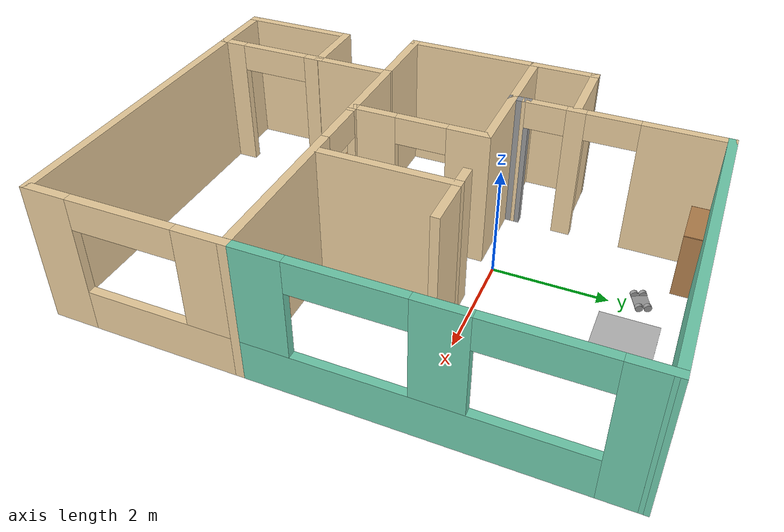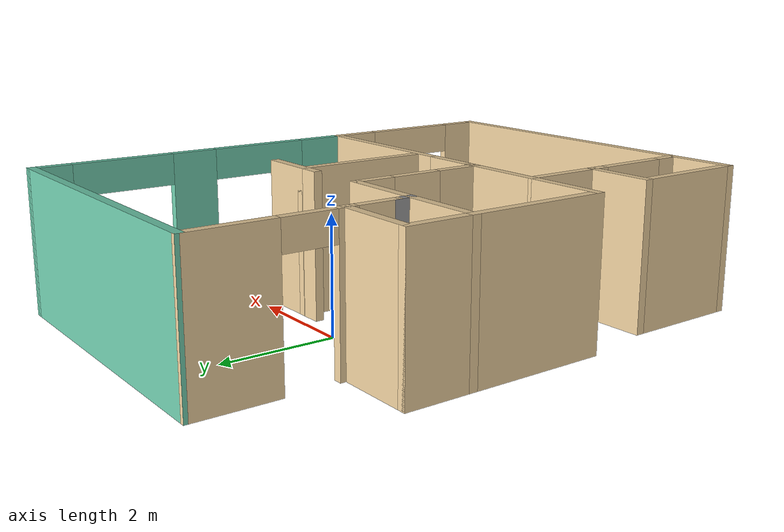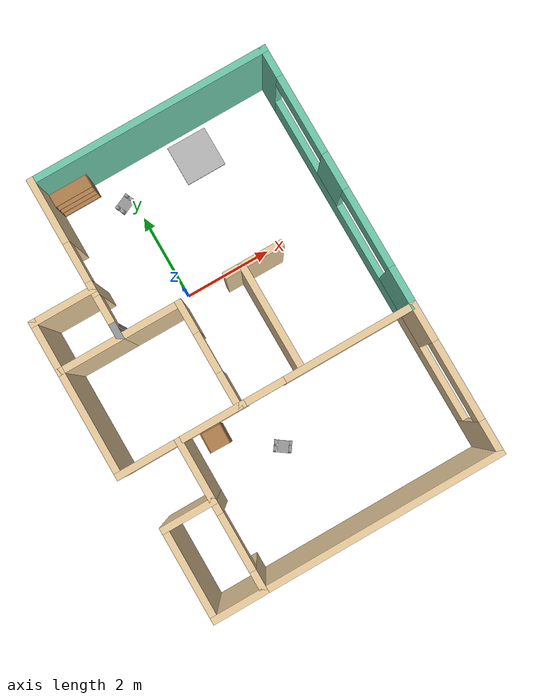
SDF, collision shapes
<?xml version='1.0'?>
<sdf version='1.6'>
  <model name='combined_model'>
    <model name='apt_1br'>
      <pose frame=''>0.440605 -1.37151 0 0 -0 0</pose>
      <link name='Wall_10'>
        <collision name='Wall_10_Collision'>
          <geometry>
            <box>
              <size>5.5 0.15 2.5</size>
            </box>
          </geometry>
          <pose frame=''>0 0 1.25 0 -0 0</pose>
        </collision>
        <visual name='Wall_10_Visual'>
          <pose frame=''>0 0 1.25 0 -0 0</pose>
          <geometry>
            <box>
              <size>5.5 0.15 2.5</size>
            </box>
          </geometry>
          <material>
            <script>
              <uri>file://media/materials/scripts/gazebo.material</uri>
              <name>Gazebo/Grey</name>
            </script>
            <ambient>0.921569 0.807843 0.615686 1</ambient>
          </material>
          <meta>
            <layer>0</layer>
          </meta>
        </visual>
        <pose frame=''>0.674919 -4.65002 0 0 -0 3.14159</pose>
      </link>
      <link name='Wall_21'>
        <collision name='Wall_21_Collision'>
          <geometry>
            <box>
              <size>1.5 0.15 2.5</size>
            </box>
          </geometry>
          <pose frame=''>0 0 1.25 0 -0 0</pose>
        </collision>
        <visual name='Wall_21_Visual'>
          <pose frame=''>0 0 1.25 0 -0 0</pose>
          <geometry>
            <box>
              <size>1.5 0.15 2.5</size>
            </box>
          </geometry>
          <material>
            <script>
              <uri>file://media/materials/scripts/gazebo.material</uri>
              <name>Gazebo/Grey</name>
            </script>
            <ambient>0.921569 0.807843 0.615686 1</ambient>
          </material>
          <meta>
            <layer>0</layer>
          </meta>
        </visual>
        <pose frame=''>-1.32508 1.04998 0 0 -0 3.14159</pose>
      </link>
      <link name='Wall_29'>
        <pose frame=''>3.34992 1.67498 0 0 -0 -1.5708</pose>
        <visual name='Wall_29_Visual_0'>
          <pose frame=''>-2.69448 0 1.25 0 -0 0</pose>
          <geometry>
            <box>
              <size>0.71105 0.15 2.5</size>
            </box>
          </geometry>
          <material>
            <script>
              <uri>file://media/materials/scripts/gazebo.material</uri>
              <name>Gazebo/Grey</name>
            </script>
            <ambient>0.435294 0.796078 0.67451 1</ambient>
          </material>
          <meta>
            <layer>0</layer>
          </meta>
        </visual>
        <collision name='Wall_29_Collision_0'>
          <geometry>
            <box>
              <size>0.71105 0.15 2.5</size>
            </box>
          </geometry>
          <pose frame=''>-2.69448 0 1.25 0 -0 0</pose>
        </collision>
        <visual name='Wall_29_Visual_1'>
          <pose frame=''>0.355525 0 0.375 0 -0 0</pose>
          <geometry>
            <box>
              <size>5.38895 0.15 0.75</size>
            </box>
          </geometry>
          <material>
            <script>
              <uri>file://media/materials/scripts/gazebo.material</uri>
              <name>Gazebo/Grey</name>
            </script>
            <ambient>0.435294 0.796078 0.67451 1</ambient>
          </material>
          <meta>
            <layer>0</layer>
          </meta>
        </visual>
        <collision name='Wall_29_Collision_1'>
          <geometry>
            <box>
              <size>5.38895 0.15 0.75</size>
            </box>
          </geometry>
          <pose frame=''>0.355525 0 0.375 0 -0 0</pose>
        </collision>
        <visual name='Wall_29_Visual_2'>
          <pose frame=''>-0.124805 0 1.625 0 -0 0</pose>
          <geometry>
            <box>
              <size>0.82829 0.15 1.75</size>
            </box>
          </geometry>
          <material>
            <script>
              <uri>file://media/materials/scripts/gazebo.material</uri>
              <name>Gazebo/Grey</name>
            </script>
            <ambient>0.435294 0.796078 0.67451 1</ambient>
          </material>
          <meta>
            <layer>0</layer>
          </meta>
        </visual>
        <collision name='Wall_29_Collision_2'>
          <geometry>
            <box>
              <size>0.82829 0.15 1.75</size>
            </box>
          </geometry>
          <pose frame=''>-0.124805 0 1.625 0 -0 0</pose>
        </collision>
        <visual name='Wall_29_Visual_3'>
          <pose frame=''>2.56967 0 1.625 0 -0 0</pose>
          <geometry>
            <box>
              <size>0.96066 0.15 1.75</size>
            </box>
          </geometry>
          <material>
            <script>
              <uri>file://media/materials/scripts/gazebo.material</uri>
              <name>Gazebo/Grey</name>
            </script>
            <ambient>0.435294 0.796078 0.67451 1</ambient>
          </material>
          <meta>
            <layer>0</layer>
          </meta>
        </visual>
        <collision name='Wall_29_Collision_3'>
          <geometry>
            <box>
              <size>0.96066 0.15 1.75</size>
            </box>
          </geometry>
          <pose frame=''>2.56967 0 1.625 0 -0 0</pose>
        </collision>
        <visual name='Wall_29_Visual_4'>
          <pose frame=''>-1.43895 0 2.225 0 -0 0</pose>
          <geometry>
            <box>
              <size>1.8 0.15 0.55</size>
            </box>
          </geometry>
          <material>
            <script>
              <uri>file://media/materials/scripts/gazebo.material</uri>
              <name>Gazebo/Grey</name>
            </script>
            <ambient>0.435294 0.796078 0.67451 1</ambient>
          </material>
          <meta>
            <layer>0</layer>
          </meta>
        </visual>
        <collision name='Wall_29_Collision_4'>
          <geometry>
            <box>
              <size>1.8 0.15 0.55</size>
            </box>
          </geometry>
          <pose frame=''>-1.43895 0 2.225 0 -0 0</pose>
        </collision>
        <visual name='Wall_29_Visual_5'>
          <pose frame=''>1.18934 0 2.225 0 -0 0</pose>
          <geometry>
            <box>
              <size>1.8 0.15 0.55</size>
            </box>
          </geometry>
          <material>
            <script>
              <uri>file://media/materials/scripts/gazebo.material</uri>
              <name>Gazebo/Grey</name>
            </script>
            <ambient>0.435294 0.796078 0.67451 1</ambient>
          </material>
          <meta>
            <layer>0</layer>
          </meta>
        </visual>
        <collision name='Wall_29_Collision_5'>
          <geometry>
            <box>
              <size>1.8 0.15 0.55</size>
            </box>
          </geometry>
          <pose frame=''>1.18934 0 2.225 0 -0 0</pose>
        </collision>
      </link>
      <link name='Wall_31'>
        <pose frame=''>3.34992 -2.97502 0 0 -0 1.5708</pose>
        <visual name='Wall_31_Visual_0'>
          <pose frame=''>-1.34686 0 1.25 0 -0 0</pose>
          <geometry>
            <box>
              <size>0.806273 0.15 2.5</size>
            </box>
          </geometry>
          <material>
            <script>
              <uri>file://media/materials/scripts/gazebo.material</uri>
              <name>Gazebo/Grey</name>
            </script>
            <ambient>0.921569 0.807843 0.615686 1</ambient>
          </material>
          <meta>
            <layer>0</layer>
          </meta>
        </visual>
        <collision name='Wall_31_Collision_0'>
          <geometry>
            <box>
              <size>0.806273 0.15 2.5</size>
            </box>
          </geometry>
          <pose frame=''>-1.34686 0 1.25 0 -0 0</pose>
        </collision>
        <visual name='Wall_31_Visual_1'>
          <pose frame=''>0.403136 0 0.375 0 -0 0</pose>
          <geometry>
            <box>
              <size>2.69373 0.15 0.75</size>
            </box>
          </geometry>
          <material>
            <script>
              <uri>file://media/materials/scripts/gazebo.material</uri>
              <name>Gazebo/Grey</name>
            </script>
            <ambient>0.921569 0.807843 0.615686 1</ambient>
          </material>
          <meta>
            <layer>0</layer>
          </meta>
        </visual>
        <collision name='Wall_31_Collision_1'>
          <geometry>
            <box>
              <size>2.69373 0.15 0.75</size>
            </box>
          </geometry>
          <pose frame=''>0.403136 0 0.375 0 -0 0</pose>
        </collision>
        <visual name='Wall_31_Visual_2'>
          <pose frame=''>1.30314 0 1.625 0 -0 0</pose>
          <geometry>
            <box>
              <size>0.893727 0.15 1.75</size>
            </box>
          </geometry>
          <material>
            <script>
              <uri>file://media/materials/scripts/gazebo.material</uri>
              <name>Gazebo/Grey</name>
            </script>
            <ambient>0.921569 0.807843 0.615686 1</ambient>
          </material>
          <meta>
            <layer>0</layer>
          </meta>
        </visual>
        <collision name='Wall_31_Collision_2'>
          <geometry>
            <box>
              <size>0.893727 0.15 1.75</size>
            </box>
          </geometry>
          <pose frame=''>1.30314 0 1.625 0 -0 0</pose>
        </collision>
        <visual name='Wall_31_Visual_3'>
          <pose frame=''>-0.043727 0 2.225 0 -0 0</pose>
          <geometry>
            <box>
              <size>1.8 0.15 0.55</size>
            </box>
          </geometry>
          <material>
            <script>
              <uri>file://media/materials/scripts/gazebo.material</uri>
              <name>Gazebo/Grey</name>
            </script>
            <ambient>0.921569 0.807843 0.615686 1</ambient>
          </material>
          <meta>
            <layer>0</layer>
          </meta>
        </visual>
        <collision name='Wall_31_Collision_3'>
          <geometry>
            <box>
              <size>1.8 0.15 0.55</size>
            </box>
          </geometry>
          <pose frame=''>-0.043727 0 2.225 0 -0 0</pose>
        </collision>
      </link>
      <link name='Wall_33'>
        <pose frame=''>-0.650081 -0.125024 0 0 -0 -1.5708</pose>
        <visual name='Wall_33_Visual_0'>
          <pose frame=''>-0.874194 0 1.25 0 -0 0</pose>
          <geometry>
            <box>
              <size>0.751611 0.15 2.5</size>
            </box>
          </geometry>
          <material>
            <script>
              <uri>file://media/materials/scripts/gazebo.material</uri>
              <name>Gazebo/Grey</name>
            </script>
            <ambient>0.921569 0.807843 0.615686 1</ambient>
          </material>
          <meta>
            <layer>0</layer>
          </meta>
        </visual>
        <collision name='Wall_33_Collision_0'>
          <geometry>
            <box>
              <size>0.751611 0.15 2.5</size>
            </box>
          </geometry>
          <pose frame=''>-0.874194 0 1.25 0 -0 0</pose>
        </collision>
        <visual name='Wall_33_Visual_1'>
          <pose frame=''>0.825806 0 1.25 0 -0 0</pose>
          <geometry>
            <box>
              <size>0.848389 0.15 2.5</size>
            </box>
          </geometry>
          <material>
            <script>
              <uri>file://media/materials/scripts/gazebo.material</uri>
              <name>Gazebo/Grey</name>
            </script>
            <ambient>0.921569 0.807843 0.615686 1</ambient>
          </material>
          <meta>
            <layer>0</layer>
          </meta>
        </visual>
        <collision name='Wall_33_Collision_1'>
          <geometry>
            <box>
              <size>0.848389 0.15 2.5</size>
            </box>
          </geometry>
          <pose frame=''>0.825806 0 1.25 0 -0 0</pose>
        </collision>
        <visual name='Wall_33_Visual_2'>
          <pose frame=''>-0.048389 0 2.25 0 -0 0</pose>
          <geometry>
            <box>
              <size>0.9 0.15 0.5</size>
            </box>
          </geometry>
          <material>
            <script>
              <uri>file://media/materials/scripts/gazebo.material</uri>
              <name>Gazebo/Grey</name>
            </script>
            <ambient>0.921569 0.807843 0.615686 1</ambient>
          </material>
          <meta>
            <layer>0</layer>
          </meta>
        </visual>
        <collision name='Wall_33_Collision_2'>
          <geometry>
            <box>
              <size>0.9 0.15 0.5</size>
            </box>
          </geometry>
          <pose frame=''>-0.048389 0 2.25 0 -0 0</pose>
        </collision>
      </link>
      <link name='Wall_34'>
        <collision name='Wall_34_Collision'>
          <geometry>
            <box>
              <size>1.5 0.15 2.5</size>
            </box>
          </geometry>
          <pose frame=''>0 0 1.25 0 -0 0</pose>
        </collision>
        <visual name='Wall_34_Visual'>
          <pose frame=''>0 0 1.25 0 -0 0</pose>
          <geometry>
            <box>
              <size>1.5 0.15 2.5</size>
            </box>
          </geometry>
          <material>
            <script>
              <uri>file://media/materials/scripts/gazebo.material</uri>
              <name>Gazebo/Grey</name>
            </script>
            <ambient>0.921569 0.807843 0.615686 1</ambient>
          </material>
          <meta>
            <layer>0</layer>
          </meta>
        </visual>
        <pose frame=''>-1.32508 -1.30002 0 0 -0 3.14159</pose>
      </link>
      <link name='Wall_36'>
        <pose frame=''>1.34992 -1.30002 0 0 -0 0</pose>
        <visual name='Wall_36_Visual_0'>
          <pose frame=''>-1.96133 0 1.25 0 -0 0</pose>
          <geometry>
            <box>
              <size>0.227341 0.15 2.5</size>
            </box>
          </geometry>
          <material>
            <script>
              <uri>file://media/materials/scripts/gazebo.material</uri>
              <name>Gazebo/Grey</name>
            </script>
            <ambient>0.921569 0.807843 0.615686 1</ambient>
          </material>
          <meta>
            <layer>0</layer>
          </meta>
        </visual>
        <collision name='Wall_36_Collision_0'>
          <geometry>
            <box>
              <size>0.227341 0.15 2.5</size>
            </box>
          </geometry>
          <pose frame=''>-1.96133 0 1.25 0 -0 0</pose>
        </collision>
        <visual name='Wall_36_Visual_1'>
          <pose frame=''>0.56367 0 1.25 0 -0 0</pose>
          <geometry>
            <box>
              <size>3.02266 0.15 2.5</size>
            </box>
          </geometry>
          <material>
            <script>
              <uri>file://media/materials/scripts/gazebo.material</uri>
              <name>Gazebo/Grey</name>
            </script>
            <ambient>0.921569 0.807843 0.615686 1</ambient>
          </material>
          <meta>
            <layer>0</layer>
          </meta>
        </visual>
        <collision name='Wall_36_Collision_1'>
          <geometry>
            <box>
              <size>3.02266 0.15 2.5</size>
            </box>
          </geometry>
          <pose frame=''>0.56367 0 1.25 0 -0 0</pose>
        </collision>
        <visual name='Wall_36_Visual_2'>
          <pose frame=''>-1.39766 0 2.25 0 -0 0</pose>
          <geometry>
            <box>
              <size>0.9 0.15 0.5</size>
            </box>
          </geometry>
          <material>
            <script>
              <uri>file://media/materials/scripts/gazebo.material</uri>
              <name>Gazebo/Grey</name>
            </script>
            <ambient>0.921569 0.807843 0.615686 1</ambient>
          </material>
          <meta>
            <layer>0</layer>
          </meta>
        </visual>
        <collision name='Wall_36_Collision_2'>
          <geometry>
            <box>
              <size>0.9 0.15 0.5</size>
            </box>
          </geometry>
          <pose frame=''>-1.39766 0 2.25 0 -0 0</pose>
        </collision>
      </link>
      <link name='Wall_38'>
        <collision name='Wall_38_Collision'>
          <geometry>
            <box>
              <size>2.5 0.15 2.5</size>
            </box>
          </geometry>
          <pose frame=''>0 0 1.25 0 -0 0</pose>
        </collision>
        <visual name='Wall_38_Visual'>
          <pose frame=''>0 0 1.25 0 -0 0</pose>
          <geometry>
            <box>
              <size>2.5 0.15 2.5</size>
            </box>
          </geometry>
          <material>
            <script>
              <uri>file://media/materials/scripts/gazebo.material</uri>
              <name>Gazebo/Grey</name>
            </script>
            <ambient>0.921569 0.807843 0.615686 1</ambient>
          </material>
          <meta>
            <layer>0</layer>
          </meta>
        </visual>
        <pose frame=''>0.806186 -0.096149 0 0 -0 1.5708</pose>
      </link>
      <link name='Wall_41'>
        <collision name='Wall_41_Collision'>
          <geometry>
            <box>
              <size>1 0.15 2.5</size>
            </box>
          </geometry>
          <pose frame=''>0 0 1.25 0 -0 0</pose>
        </collision>
        <visual name='Wall_41_Visual'>
          <pose frame=''>0 0 1.25 0 -0 0</pose>
          <geometry>
            <box>
              <size>1 0.15 2.5</size>
            </box>
          </geometry>
          <material>
            <script>
              <uri>file://media/materials/scripts/gazebo.material</uri>
              <name>Gazebo/Grey</name>
            </script>
            <ambient>0.921569 0.807843 0.615686 1</ambient>
          </material>
          <meta>
            <layer>0</layer>
          </meta>
        </visual>
        <pose frame=''>1.23119 1.07885 0 0 -0 0</pose>
      </link>
      <link name='Wall_43'>
        <collision name='Wall_43_Collision'>
          <geometry>
            <box>
              <size>0.5 0.15 2.5</size>
            </box>
          </geometry>
          <pose frame=''>0 0 1.25 0 -0 0</pose>
        </collision>
        <visual name='Wall_43_Visual'>
          <pose frame=''>0 0 1.25 0 -0 0</pose>
          <geometry>
            <box>
              <size>0.5 0.15 2.5</size>
            </box>
          </geometry>
          <material>
            <script>
              <uri>file://media/materials/scripts/gazebo.material</uri>
              <name>Gazebo/Grey</name>
            </script>
            <ambient>0.921569 0.807843 0.615686 1</ambient>
          </material>
          <meta>
            <layer>0</layer>
          </meta>
        </visual>
        <pose frame=''>0.631186 1.07885 0 0 -0 3.14159</pose>
      </link>
      <link name='Wall_5'>
        <pose frame=''>-2.00008 2.96898 0 0 -0 1.5708</pose>
        <visual name='Wall_5_Visual_0'>
          <pose frame=''>-1.71167 0 1.25 0 -0 0</pose>
          <geometry>
            <box>
              <size>0.064664 0.15 2.5</size>
            </box>
          </geometry>
          <material>
            <script>
              <uri>file://media/materials/scripts/gazebo.material</uri>
              <name>Gazebo/Grey</name>
            </script>
            <ambient>0.921569 0.807843 0.615686 1</ambient>
          </material>
          <meta>
            <layer>0</layer>
          </meta>
        </visual>
        <collision name='Wall_5_Collision_0'>
          <geometry>
            <box>
              <size>0.064664 0.15 2.5</size>
            </box>
          </geometry>
          <pose frame=''>-1.71167 0 1.25 0 -0 0</pose>
        </collision>
        <visual name='Wall_5_Visual_1'>
          <pose frame=''>-0.81386 0 1.25 0 -0 0</pose>
          <geometry>
            <box>
              <size>0.330951 0.15 2.5</size>
            </box>
          </geometry>
          <material>
            <script>
              <uri>file://media/materials/scripts/gazebo.material</uri>
              <name>Gazebo/Grey</name>
            </script>
            <ambient>0.921569 0.807843 0.615686 1</ambient>
          </material>
          <meta>
            <layer>0</layer>
          </meta>
        </visual>
        <collision name='Wall_5_Collision_1'>
          <geometry>
            <box>
              <size>0.330951 0.15 2.5</size>
            </box>
          </geometry>
          <pose frame=''>-0.81386 0 1.25 0 -0 0</pose>
        </collision>
        <visual name='Wall_5_Visual_2'>
          <pose frame=''>0.997808 0 1.25 0 -0 0</pose>
          <geometry>
            <box>
              <size>1.49239 0.15 2.5</size>
            </box>
          </geometry>
          <material>
            <script>
              <uri>file://media/materials/scripts/gazebo.material</uri>
              <name>Gazebo/Grey</name>
            </script>
            <ambient>0.921569 0.807843 0.615686 1</ambient>
          </material>
          <meta>
            <layer>0</layer>
          </meta>
        </visual>
        <collision name='Wall_5_Collision_2'>
          <geometry>
            <box>
              <size>1.49239 0.15 2.5</size>
            </box>
          </geometry>
          <pose frame=''>0.997808 0 1.25 0 -0 0</pose>
        </collision>
        <visual name='Wall_5_Visual_3'>
          <pose frame=''>-1.32934 0 2.25 0 -0 0</pose>
          <geometry>
            <box>
              <size>0.7 0.15 0.5</size>
            </box>
          </geometry>
          <material>
            <script>
              <uri>file://media/materials/scripts/gazebo.material</uri>
              <name>Gazebo/Grey</name>
            </script>
            <ambient>0.921569 0.807843 0.615686 1</ambient>
          </material>
          <meta>
            <layer>0</layer>
          </meta>
        </visual>
        <collision name='Wall_5_Collision_3'>
          <geometry>
            <box>
              <size>0.7 0.15 0.5</size>
            </box>
          </geometry>
          <pose frame=''>-1.32934 0 2.25 0 -0 0</pose>
        </collision>
        <visual name='Wall_5_Visual_4'>
          <pose frame=''>-0.198385 0 2.25 0 -0 0</pose>
          <geometry>
            <box>
              <size>0.9 0.15 0.5</size>
            </box>
          </geometry>
          <material>
            <script>
              <uri>file://media/materials/scripts/gazebo.material</uri>
              <name>Gazebo/Grey</name>
            </script>
            <ambient>0.921569 0.807843 0.615686 1</ambient>
          </material>
          <meta>
            <layer>0</layer>
          </meta>
        </visual>
        <collision name='Wall_5_Collision_4'>
          <geometry>
            <box>
              <size>0.9 0.15 0.5</size>
            </box>
          </geometry>
          <pose frame=''>-0.198385 0 2.25 0 -0 0</pose>
        </collision>
      </link>
      <link name='Wall_54'>
        <collision name='Wall_54_Collision'>
          <geometry>
            <box>
              <size>1.5 0.15 2.5</size>
            </box>
          </geometry>
          <pose frame=''>0 0 1.25 0 -0 0</pose>
        </collision>
        <visual name='Wall_54_Visual'>
          <pose frame=''>0 0 1.25 0 -0 0</pose>
          <geometry>
            <box>
              <size>1.5 0.15 2.5</size>
            </box>
          </geometry>
          <material>
            <script>
              <uri>file://media/materials/scripts/gazebo.material</uri>
              <name>Gazebo/Grey</name>
            </script>
            <ambient>0.921569 0.807843 0.615686 1</ambient>
          </material>
          <meta>
            <layer>0</layer>
          </meta>
        </visual>
        <pose frame=''>-2.67508 1.04998 0 0 -0 3.14159</pose>
      </link>
      <link name='Wall_55'>
        <collision name='Wall_55_Collision'>
          <geometry>
            <box>
              <size>2.5 0.15 2.5</size>
            </box>
          </geometry>
          <pose frame=''>0 0 1.25 0 -0 0</pose>
        </collision>
        <visual name='Wall_55_Visual'>
          <pose frame=''>0 0 1.25 0 -0 0</pose>
          <geometry>
            <box>
              <size>2.5 0.15 2.5</size>
            </box>
          </geometry>
          <material>
            <script>
              <uri>file://media/materials/scripts/gazebo.material</uri>
              <name>Gazebo/Grey</name>
            </script>
            <ambient>0.921569 0.807843 0.615686 1</ambient>
          </material>
          <meta>
            <layer>0</layer>
          </meta>
        </visual>
        <pose frame=''>-3.35008 -0.125024 0 0 -0 -1.5708</pose>
      </link>
      <link name='Wall_56'>
        <collision name='Wall_56_Collision'>
          <geometry>
            <box>
              <size>1.5 0.15 2.5</size>
            </box>
          </geometry>
          <pose frame=''>0 0 1.25 0 -0 0</pose>
        </collision>
        <visual name='Wall_56_Visual'>
          <pose frame=''>0 0 1.25 0 -0 0</pose>
          <geometry>
            <box>
              <size>1.5 0.15 2.5</size>
            </box>
          </geometry>
          <material>
            <script>
              <uri>file://media/materials/scripts/gazebo.material</uri>
              <name>Gazebo/Grey</name>
            </script>
            <ambient>0.921569 0.807843 0.615686 1</ambient>
          </material>
          <meta>
            <layer>0</layer>
          </meta>
        </visual>
        <pose frame=''>-2.67508 -1.30002 0 0 -0 0</pose>
      </link>
      <link name='Wall_57'>
        <collision name='Wall_57_Collision'>
          <geometry>
            <box>
              <size>1.5 0.15 2.5</size>
            </box>
          </geometry>
          <pose frame=''>0 0 1.25 0 -0 0</pose>
        </collision>
        <visual name='Wall_57_Visual'>
          <pose frame=''>0 0 1.25 0 -0 0</pose>
          <geometry>
            <box>
              <size>1.5 0.15 2.5</size>
            </box>
          </geometry>
          <material>
            <script>
              <uri>file://media/materials/scripts/gazebo.material</uri>
              <name>Gazebo/Grey</name>
            </script>
            <ambient>0.921569 0.807843 0.615686 1</ambient>
          </material>
          <meta>
            <layer>0</layer>
          </meta>
        </visual>
        <pose frame=''>-2.0017 -1.97502 0 0 -0 -1.57319</pose>
      </link>
      <link name='Wall_58'>
        <collision name='Wall_58_Collision'>
          <geometry>
            <box>
              <size>1.247 0.15 2.5</size>
            </box>
          </geometry>
          <pose frame=''>0 0 1.25 0 -0 0</pose>
        </collision>
        <visual name='Wall_58_Visual'>
          <pose frame=''>0 0 1.25 0 -0 0</pose>
          <geometry>
            <box>
              <size>1.247 0.15 2.5</size>
            </box>
          </geometry>
          <material>
            <script>
              <uri>file://media/materials/scripts/gazebo.material</uri>
              <name>Gazebo/Grey</name>
            </script>
            <ambient>0.921569 0.807843 0.615686 1</ambient>
          </material>
          <meta>
            <layer>0</layer>
          </meta>
        </visual>
        <pose frame=''>-2.55181 -2.65002 0 0 -0 3.14159</pose>
      </link>
      <link name='Wall_6'>
        <collision name='Wall_6_Collision'>
          <geometry>
            <box>
              <size>5.5 0.15 2.5</size>
            </box>
          </geometry>
          <pose frame=''>0 0 1.25 0 -0 0</pose>
        </collision>
        <visual name='Wall_6_Visual'>
          <pose frame=''>0 0 1.25 0 -0 0</pose>
          <geometry>
            <box>
              <size>5.5 0.15 2.5</size>
            </box>
          </geometry>
          <material>
            <script>
              <uri>file://media/materials/scripts/gazebo.material</uri>
              <name>Gazebo/Grey</name>
            </script>
            <ambient>0.435294 0.796078 0.67451 1</ambient>
          </material>
          <meta>
            <layer>0</layer>
          </meta>
        </visual>
        <pose frame=''>0.674919 4.64398 0 0 -0 0.002243</pose>
      </link>
      <link name='Wall_62'>
        <collision name='Wall_62_Collision'>
          <geometry>
            <box>
              <size>1.25 0.15 2.5</size>
            </box>
          </geometry>
          <pose frame=''>0 0 1.25 0 -0 0</pose>
        </collision>
        <visual name='Wall_62_Visual'>
          <pose frame=''>0 0 1.25 0 -0 0</pose>
          <geometry>
            <box>
              <size>1.25 0.15 2.5</size>
            </box>
          </geometry>
          <material>
            <script>
              <uri>file://media/materials/scripts/gazebo.material</uri>
              <name>Gazebo/Grey</name>
            </script>
            <ambient>0.921569 0.807843 0.615686 1</ambient>
          </material>
          <meta>
            <layer>0</layer>
          </meta>
        </visual>
        <pose frame=''>-2.55008 -4.65002 0 0 -0 3.14159</pose>
      </link>
      <link name='Wall_63'>
        <collision name='Wall_63_Collision'>
          <geometry>
            <box>
              <size>2 0.15 2.5</size>
            </box>
          </geometry>
          <pose frame=''>0 0 1.25 0 -0 0</pose>
        </collision>
        <visual name='Wall_63_Visual'>
          <pose frame=''>0 0 1.25 0 -0 0</pose>
          <geometry>
            <box>
              <size>2 0.15 2.5</size>
            </box>
          </geometry>
          <material>
            <script>
              <uri>file://media/materials/scripts/gazebo.material</uri>
              <name>Gazebo/Grey</name>
            </script>
            <ambient>0.921569 0.807843 0.615686 1</ambient>
          </material>
          <meta>
            <layer>0</layer>
          </meta>
        </visual>
        <pose frame=''>-3.10008 -3.72502 0 0 -0 1.5708</pose>
      </link>
      <link name='Wall_65'>
        <pose frame=''>-2.0017 -3.65002 0 0 -0 -1.56918</pose>
        <visual name='Wall_65_Visual_0'>
          <pose frame=''>-0.895757 0 1.25 0 -0 0</pose>
          <geometry>
            <box>
              <size>0.358489 0.15 2.5</size>
            </box>
          </geometry>
          <material>
            <script>
              <uri>file://media/materials/scripts/gazebo.material</uri>
              <name>Gazebo/Grey</name>
            </script>
            <ambient>0.921569 0.807843 0.615686 1</ambient>
          </material>
          <meta>
            <layer>0</layer>
          </meta>
        </visual>
        <collision name='Wall_65_Collision_0'>
          <geometry>
            <box>
              <size>0.358489 0.15 2.5</size>
            </box>
          </geometry>
          <pose frame=''>-0.895757 0 1.25 0 -0 0</pose>
        </collision>
        <visual name='Wall_65_Visual_1'>
          <pose frame=''>0.815925 0 1.25 0 -0 0</pose>
          <geometry>
            <box>
              <size>0.518152 0.15 2.5</size>
            </box>
          </geometry>
          <material>
            <script>
              <uri>file://media/materials/scripts/gazebo.material</uri>
              <name>Gazebo/Grey</name>
            </script>
            <ambient>0.921569 0.807843 0.615686 1</ambient>
          </material>
          <meta>
            <layer>0</layer>
          </meta>
        </visual>
        <collision name='Wall_65_Collision_1'>
          <geometry>
            <box>
              <size>0.518152 0.15 2.5</size>
            </box>
          </geometry>
          <pose frame=''>0.815925 0 1.25 0 -0 0</pose>
        </collision>
        <visual name='Wall_65_Visual_2'>
          <pose frame=''>-0.079832 0 2.25 0 -0 0</pose>
          <geometry>
            <box>
              <size>1.27336 0.15 0.5</size>
            </box>
          </geometry>
          <material>
            <script>
              <uri>file://media/materials/scripts/gazebo.material</uri>
              <name>Gazebo/Grey</name>
            </script>
            <ambient>0.921569 0.807843 0.615686 1</ambient>
          </material>
          <meta>
            <layer>0</layer>
          </meta>
        </visual>
        <collision name='Wall_65_Collision_2'>
          <geometry>
            <box>
              <size>1.27336 0.15 0.5</size>
            </box>
          </geometry>
          <pose frame=''>-0.079832 0 2.25 0 -0 0</pose>
        </collision>
      </link>
      <link name='Wall_70'>
        <collision name='Wall_70_Collision'>
          <geometry>
            <box>
              <size>1.25 0.15 2.5</size>
            </box>
          </geometry>
          <pose frame=''>0 0 1.25 0 -0 0</pose>
        </collision>
        <visual name='Wall_70_Visual'>
          <pose frame=''>0 0 1.25 0 -0 0</pose>
          <geometry>
            <box>
              <size>1.25 0.15 2.5</size>
            </box>
          </geometry>
          <material>
            <script>
              <uri>file://media/materials/scripts/gazebo.material</uri>
              <name>Gazebo/Grey</name>
            </script>
            <ambient>0.921569 0.807843 0.615686 1</ambient>
          </material>
          <meta>
            <layer>0</layer>
          </meta>
        </visual>
        <pose frame=''>-3.35008 1.59998 0 0 -0 1.5708</pose>
      </link>
      <link name='Wall_71'>
        <collision name='Wall_71_Collision'>
          <geometry>
            <box>
              <size>1.5 0.15 2.5</size>
            </box>
          </geometry>
          <pose frame=''>0 0 1.25 0 -0 0</pose>
        </collision>
        <visual name='Wall_71_Visual'>
          <pose frame=''>0 0 1.25 0 -0 0</pose>
          <geometry>
            <box>
              <size>1.5 0.15 2.5</size>
            </box>
          </geometry>
          <material>
            <script>
              <uri>file://media/materials/scripts/gazebo.material</uri>
              <name>Gazebo/Grey</name>
            </script>
            <ambient>0.921569 0.807843 0.615686 1</ambient>
          </material>
          <meta>
            <layer>0</layer>
          </meta>
        </visual>
        <pose frame=''>-2.67508 2.14998 0 0 -0 0</pose>
      </link>
      <link name='Wall_73'>
        <collision name='Wall_73_Collision'>
          <geometry>
            <box>
              <size>0.4 0.15 2.5</size>
            </box>
          </geometry>
          <pose frame=''>0 0 1.25 0 -0 0</pose>
        </collision>
        <visual name='Wall_73_Visual'>
          <pose frame=''>0 0 1.25 0 -0 0</pose>
          <geometry>
            <box>
              <size>0.4 0.15 2.5</size>
            </box>
          </geometry>
          <material>
            <script>
              <uri>file://media/materials/scripts/gazebo.material</uri>
              <name>Gazebo/Grey</name>
            </script>
            <ambient>1 1 1 1</ambient>
          </material>
          <meta>
            <layer>0</layer>
          </meta>
        </visual>
        <pose frame=''>-2.00008 1.17498 0 0 -0 1.5708</pose>
      </link>
      <static>1</static>
    </model>
    <model name='bookshelf'>
      <static>1</static>
      <link name='link'>
        <inertial>
          <mass>1</mass>
        </inertial>
        <collision name='back'>
          <pose frame=''>0 0.005 0.6 0 -0 0</pose>
          <geometry>
            <box>
              <size>0.9 0.01 1.2</size>
            </box>
          </geometry>
        </collision>
        <visual name='visual1'>
          <pose frame=''>0 0.005 0.6 0 -0 0</pose>
          <geometry>
            <box>
              <size>0.9 0.01 1.2</size>
            </box>
          </geometry>
          <material>
            <script>
              <uri>file://media/materials/scripts/gazebo.material</uri>
              <name>Gazebo/Wood</name>
            </script>
          </material>
        </visual>
        <collision name='left_side'>
          <pose frame=''>0.45 -0.195 0.6 0 -0 0</pose>
          <geometry>
            <box>
              <size>0.02 0.4 1.2</size>
            </box>
          </geometry>
        </collision>
        <visual name='visual2'>
          <pose frame=''>0.45 -0.195 0.6 0 -0 0</pose>
          <geometry>
            <box>
              <size>0.02 0.4 1.2</size>
            </box>
          </geometry>
          <material>
            <script>
              <uri>file://media/materials/scripts/gazebo.material</uri>
              <name>Gazebo/Wood</name>
            </script>
          </material>
        </visual>
        <collision name='right_side'>
          <pose frame=''>-0.45 -0.195 0.6 0 -0 0</pose>
          <geometry>
            <box>
              <size>0.02 0.4 1.2</size>
            </box>
          </geometry>
        </collision>
        <visual name='visual3'>
          <pose frame=''>-0.45 -0.195 0.6 0 -0 0</pose>
          <geometry>
            <box>
              <size>0.02 0.4 1.2</size>
            </box>
          </geometry>
          <material>
            <script>
              <uri>file://media/materials/scripts/gazebo.material</uri>
              <name>Gazebo/Wood</name>
            </script>
          </material>
        </visual>
        <collision name='bottom'>
          <pose frame=''>0 -0.195 0.03 0 -0 0</pose>
          <geometry>
            <box>
              <size>0.88 0.4 0.06</size>
            </box>
          </geometry>
        </collision>
        <visual name='visual4'>
          <pose frame=''>0 -0.195 0.03 0 -0 0</pose>
          <geometry>
            <box>
              <size>0.88 0.4 0.06</size>
            </box>
          </geometry>
          <material>
            <script>
              <uri>file://media/materials/scripts/gazebo.material</uri>
              <name>Gazebo/Wood</name>
            </script>
          </material>
        </visual>
        <collision name='top'>
          <pose frame=''>0 -0.195 1.19 0 -0 0</pose>
          <geometry>
            <box>
              <size>0.88 0.4 0.02</size>
            </box>
          </geometry>
        </collision>
        <visual name='visual5'>
          <pose frame=''>0 -0.195 1.19 0 -0 0</pose>
          <geometry>
            <box>
              <size>0.88 0.4 0.02</size>
            </box>
          </geometry>
          <material>
            <script>
              <uri>file://media/materials/scripts/gazebo.material</uri>
              <name>Gazebo/Wood</name>
            </script>
          </material>
        </visual>
        <collision name='low_shelf'>
          <pose frame=''>0 -0.195 0.43 0 -0 0</pose>
          <geometry>
            <box>
              <size>0.88 0.4 0.02</size>
            </box>
          </geometry>
        </collision>
        <visual name='visual6'>
          <pose frame=''>0 -0.195 0.43 0 -0 0</pose>
          <geometry>
            <box>
              <size>0.88 0.4 0.02</size>
            </box>
          </geometry>
          <material>
            <script>
              <uri>file://media/materials/scripts/gazebo.material</uri>
              <name>Gazebo/Wood</name>
            </script>
          </material>
        </visual>
        <collision name='high_shelf'>
          <pose frame=''>0 -0.195 0.8 0 -0 0</pose>
          <geometry>
            <box>
              <size>0.88 0.4 0.02</size>
            </box>
          </geometry>
        </collision>
        <visual name='visual7'>
          <pose frame=''>0 -0.195 0.8 0 -0 0</pose>
          <geometry>
            <box>
              <size>0.88 0.4 0.02</size>
            </box>
          </geometry>
          <material>
            <script>
              <uri>file://media/materials/scripts/gazebo.material</uri>
              <name>Gazebo/Wood</name>
            </script>
          </material>
        </visual>
      </link>
      <pose frame=''>-1.04171 3.29108 0 0 -0 0</pose>
    </model>
    <model name='cabinet'>
      <static>1</static>
      <link name='cabinet_bottom_plate'>
        <inertial>
          <pose frame=''>0 0 -1 0 -0 0</pose>
          <inertia>
            <ixx>2.05</ixx>
            <ixy>0</ixy>
            <ixz>0</ixz>
            <iyy>2.05</iyy>
            <iyz>0</iyz>
            <izz>2.05</izz>
          </inertia>
          <mass>25</mass>
        </inertial>
        <collision name='cabinet_bottom_plate_geom'>
          <pose frame=''>0 0 0.01 0 -0 0</pose>
          <geometry>
            <box>
              <size>0.45 0.45 0.02</size>
            </box>
          </geometry>
        </collision>
        <visual name='cabinet_bottom_plate_geom_visual'>
          <pose frame=''>0 0 0.01 0 -0 0</pose>
          <geometry>
            <box>
              <size>0.45 0.45 0.02</size>
            </box>
          </geometry>
          <material>
            <script>
              <uri>file://media/materials/scripts/gazebo.material</uri>
              <name>Gazebo/Wood</name>
            </script>
          </material>
        </visual>
        <collision name='cabinet_bottom_plate_geom_cabinet_back_plate'>
          <pose frame=''>0.235 0 0.51 0 -0 0</pose>
          <geometry>
            <box>
              <size>0.02 0.45 1.02</size>
            </box>
          </geometry>
        </collision>
        <visual name='cabinet_bottom_plate_geom_cabinet_back_plate_visual'>
          <pose frame=''>0.235 0 0.51 0 -0 0</pose>
          <geometry>
            <box>
              <size>0.02 0.45 1.02</size>
            </box>
          </geometry>
          <material>
            <script>
              <uri>file://media/materials/scripts/gazebo.material</uri>
              <name>Gazebo/Wood</name>
            </script>
          </material>
        </visual>
        <collision name='cabinet_bottom_plate_geom_cabinet_left_plate'>
          <pose frame=''>0 0.235 0.51 0 -0 0</pose>
          <geometry>
            <box>
              <size>0.45 0.02 1.02</size>
            </box>
          </geometry>
        </collision>
        <visual name='cabinet_bottom_plate_geom_cabinet_left_plate_visual'>
          <pose frame=''>0 0.235 0.51 0 -0 0</pose>
          <geometry>
            <box>
              <size>0.45 0.02 1.02</size>
            </box>
          </geometry>
          <material>
            <script>
              <uri>file://media/materials/scripts/gazebo.material</uri>
              <name>Gazebo/Wood</name>
            </script>
          </material>
        </visual>
        <collision name='cabinet_bottom_plate_geom_cabinet_middle_plate'>
          <pose frame=''>0 0 0.51 0 -0 0</pose>
          <geometry>
            <box>
              <size>0.45 0.45 0.02</size>
            </box>
          </geometry>
        </collision>
        <visual name='cabinet_bottom_plate_geom_cabinet_middle_plate_visual'>
          <pose frame=''>0 0 0.51 0 -0 0</pose>
          <geometry>
            <box>
              <size>0.45 0.45 0.02</size>
            </box>
          </geometry>
          <material>
            <script>
              <uri>file://media/materials/scripts/gazebo.material</uri>
              <name>Gazebo/Wood</name>
            </script>
          </material>
        </visual>
        <collision name='cabinet_bottom_plate_geom_cabinet_right_plate'>
          <pose frame=''>0 -0.235 0.51 0 -0 0</pose>
          <geometry>
            <box>
              <size>0.45 0.02 1.02</size>
            </box>
          </geometry>
        </collision>
        <visual name='cabinet_bottom_plate_geom_cabinet_right_plate_visual'>
          <pose frame=''>0 -0.235 0.51 0 -0 0</pose>
          <geometry>
            <box>
              <size>0.45 0.02 1.02</size>
            </box>
          </geometry>
          <material>
            <script>
              <uri>file://media/materials/scripts/gazebo.material</uri>
              <name>Gazebo/Wood</name>
            </script>
          </material>
        </visual>
        <collision name='cabinet_bottom_plate_geom_cabinet_top_plate'>
          <pose frame=''>0 0 1.01 0 -0 0</pose>
          <geometry>
            <box>
              <size>0.45 0.45 0.02</size>
            </box>
          </geometry>
        </collision>
        <visual name='cabinet_bottom_plate_geom_cabinet_top_plate_visual'>
          <pose frame=''>0 0 1.01 0 -0 0</pose>
          <geometry>
            <box>
              <size>0.45 0.45 0.02</size>
            </box>
          </geometry>
          <material>
            <script>
              <uri>file://media/materials/scripts/gazebo.material</uri>
              <name>Gazebo/Wood</name>
            </script>
          </material>
        </visual>
      </link>
      <pose frame=''>-0.989306 -2.99197 0 0 -0 1.55199</pose>
    </model>
    <model name='cafe_table'>
      <static>1</static>
      <link name='link'>
        <collision name='surface'>
          <pose frame=''>0 0 0.755 0 -0 0</pose>
          <geometry>
            <box>
              <size>0.913 0.913 0.04</size>
            </box>
          </geometry>
        </collision>
        <collision name='column'>
          <pose frame=''>0 0 0.37 0 -0 0</pose>
          <geometry>
            <box>
              <size>0.042 0.042 0.74</size>
            </box>
          </geometry>
        </collision>
        <collision name='base'>
          <pose frame=''>0 0 0.02 0 -0 0</pose>
          <geometry>
            <box>
              <size>0.56 0.56 0.04</size>
            </box>
          </geometry>
        </collision>
        <visual name='visual'>
          <geometry>
            <mesh>
              <uri>model://cafe_table/meshes/cafe_table.dae</uri>
            </mesh>
          </geometry>
        </visual>
      </link>
      <pose frame=''>1.64758 2.46156 0 0 -0 0</pose>
    </model>
    <model name='fwd_robot'>
      <link name='link_4_clone'>
        <inertial>
          <mass>1</mass>
          <inertia>
            <ixx>0.145833</ixx>
            <ixy>0</ixy>
            <ixz>0</ixz>
            <iyy>0.145833</iyy>
            <iyz>0</iyz>
            <izz>0.125</izz>
          </inertia>
          <pose frame=''>0 0 0 0 -0 0</pose>
        </inertial>
        <pose frame=''>-0.072 -0.1635 -0 1.5708 -0 0</pose>
        <gravity>1</gravity>
        <self_collide>0</self_collide>
        <kinematic>0</kinematic>
        <enable_wind>0</enable_wind>
        <visual name='visual'>
          <pose frame=''>0 0 0 0 -0 0</pose>
          <geometry>
            <cylinder>
              <radius>0.065</radius>
              <length>0.065</length>
            </cylinder>
          </geometry>
          <material>
            <lighting>1</lighting>
            <script>
              <uri>file://media/materials/scripts/gazebo.material</uri>
              <name>Gazebo/Grey</name>
            </script>
            <shader type='vertex'>
              <normal_map>__default__</normal_map>
            </shader>
            <ambient>0.3 0.3 0.3 1</ambient>
            <diffuse>0.7 0.7 0.7 1</diffuse>
            <specular>0.01 0.01 0.01 1</specular>
            <emissive>0 0 0 1</emissive>
          </material>
          <transparency>0</transparency>
          <cast_shadows>1</cast_shadows>
        </visual>
        <collision name='collision'>
          <laser_retro>0</laser_retro>
          <max_contacts>10</max_contacts>
          <pose frame=''>0 0 0 0 -0 0</pose>
          <geometry>
            <cylinder>
              <radius>0.065</radius>
              <length>0.065</length>
            </cylinder>
          </geometry>
          <surface>
            <friction>
              <ode>
                <mu>1</mu>
                <mu2>1</mu2>
                <fdir1>0 0 0</fdir1>
                <slip1>0</slip1>
                <slip2>0</slip2>
              </ode>
              <torsional>
                <coefficient>1</coefficient>
                <patch_radius>0</patch_radius>
                <surface_radius>0</surface_radius>
                <use_patch_radius>1</use_patch_radius>
                <ode>
                  <slip>0</slip>
                </ode>
              </torsional>
            </friction>
            <bounce>
              <restitution_coefficient>0</restitution_coefficient>
              <threshold>1e+06</threshold>
            </bounce>
            <contact>
              <collide_without_contact>0</collide_without_contact>
              <collide_without_contact_bitmask>1</collide_without_contact_bitmask>
              <collide_bitmask>1</collide_bitmask>
              <ode>
                <soft_cfm>0</soft_cfm>
                <soft_erp>0.2</soft_erp>
                <kp>1e+13</kp>
                <kd>1</kd>
                <max_vel>0.01</max_vel>
                <min_depth>0</min_depth>
              </ode>
              <bullet>
                <split_impulse>1</split_impulse>
                <split_impulse_penetration_threshold>-0.01</split_impulse_penetration_threshold>
                <soft_cfm>0</soft_cfm>
                <soft_erp>0.2</soft_erp>
                <kp>1e+13</kp>
                <kd>1</kd>
              </bullet>
            </contact>
          </surface>
        </collision>
      </link>
      <link name='link_4_clone_0'>
        <inertial>
          <mass>1</mass>
          <inertia>
            <ixx>0.145833</ixx>
            <ixy>0</ixy>
            <ixz>0</ixz>
            <iyy>0.145833</iyy>
            <iyz>0</iyz>
            <izz>0.125</izz>
          </inertia>
          <pose frame=''>0 0 0 0 -0 0</pose>
        </inertial>
        <pose frame=''>0.073 -0.1635 -0 1.5708 -0 0</pose>
        <gravity>1</gravity>
        <self_collide>0</self_collide>
        <kinematic>0</kinematic>
        <enable_wind>0</enable_wind>
        <visual name='visual'>
          <pose frame=''>0 0 0 0 -0 0</pose>
          <geometry>
            <cylinder>
              <radius>0.065</radius>
              <length>0.065</length>
            </cylinder>
          </geometry>
          <material>
            <lighting>1</lighting>
            <script>
              <uri>file://media/materials/scripts/gazebo.material</uri>
              <name>Gazebo/Grey</name>
            </script>
            <shader type='vertex'>
              <normal_map>__default__</normal_map>
            </shader>
            <ambient>0.3 0.3 0.3 1</ambient>
            <diffuse>0.7 0.7 0.7 1</diffuse>
            <specular>0.01 0.01 0.01 1</specular>
            <emissive>0 0 0 1</emissive>
          </material>
          <transparency>0</transparency>
          <cast_shadows>1</cast_shadows>
        </visual>
        <collision name='collision'>
          <laser_retro>0</laser_retro>
          <max_contacts>10</max_contacts>
          <pose frame=''>0 0 0 0 -0 0</pose>
          <geometry>
            <cylinder>
              <radius>0.065</radius>
              <length>0.065</length>
            </cylinder>
          </geometry>
          <surface>
            <friction>
              <ode>
                <mu>1</mu>
                <mu2>1</mu2>
                <fdir1>0 0 0</fdir1>
                <slip1>0</slip1>
                <slip2>0</slip2>
              </ode>
              <torsional>
                <coefficient>1</coefficient>
                <patch_radius>0</patch_radius>
                <surface_radius>0</surface_radius>
                <use_patch_radius>1</use_patch_radius>
                <ode>
                  <slip>0</slip>
                </ode>
              </torsional>
            </friction>
            <bounce>
              <restitution_coefficient>0</restitution_coefficient>
              <threshold>1e+06</threshold>
            </bounce>
            <contact>
              <collide_without_contact>0</collide_without_contact>
              <collide_without_contact_bitmask>1</collide_without_contact_bitmask>
              <collide_bitmask>1</collide_bitmask>
              <ode>
                <soft_cfm>0</soft_cfm>
                <soft_erp>0.2</soft_erp>
                <kp>1e+13</kp>
                <kd>1</kd>
                <max_vel>0.01</max_vel>
                <min_depth>0</min_depth>
              </ode>
              <bullet>
                <split_impulse>1</split_impulse>
                <split_impulse_penetration_threshold>-0.01</split_impulse_penetration_threshold>
                <soft_cfm>0</soft_cfm>
                <soft_erp>0.2</soft_erp>
                <kp>1e+13</kp>
                <kd>1</kd>
              </bullet>
            </contact>
          </surface>
        </collision>
      </link>
      <link name='link_4_clone_0_clone'>
        <inertial>
          <mass>1</mass>
          <inertia>
            <ixx>0.145833</ixx>
            <ixy>0</ixy>
            <ixz>0</ixz>
            <iyy>0.145833</iyy>
            <iyz>0</iyz>
            <izz>0.125</izz>
          </inertia>
          <pose frame=''>0 0 0 -0.01 0 0</pose>
        </inertial>
        <pose frame=''>0.073 0.1665 -0 -1.5708 0 0</pose>
        <gravity>1</gravity>
        <self_collide>0</self_collide>
        <kinematic>0</kinematic>
        <enable_wind>0</enable_wind>
        <visual name='visual'>
          <pose frame=''>0 0 0 0 -0 0</pose>
          <geometry>
            <cylinder>
              <radius>0.065</radius>
              <length>0.065</length>
            </cylinder>
          </geometry>
          <material>
            <lighting>1</lighting>
            <script>
              <uri>file://media/materials/scripts/gazebo.material</uri>
              <name>Gazebo/Grey</name>
            </script>
            <shader type='vertex'>
              <normal_map>__default__</normal_map>
            </shader>
            <ambient>0.3 0.3 0.3 1</ambient>
            <diffuse>0.7 0.7 0.7 1</diffuse>
            <specular>0.01 0.01 0.01 1</specular>
            <emissive>0 0 0 1</emissive>
          </material>
          <transparency>0</transparency>
          <cast_shadows>1</cast_shadows>
        </visual>
        <collision name='collision'>
          <laser_retro>0</laser_retro>
          <max_contacts>10</max_contacts>
          <pose frame=''>0 0 0 0 -0 0</pose>
          <geometry>
            <cylinder>
              <radius>0.065</radius>
              <length>0.065</length>
            </cylinder>
          </geometry>
          <surface>
            <friction>
              <ode>
                <mu>1</mu>
                <mu2>1</mu2>
                <fdir1>0 0 0</fdir1>
                <slip1>0</slip1>
                <slip2>0</slip2>
              </ode>
              <torsional>
                <coefficient>1</coefficient>
                <patch_radius>0</patch_radius>
                <surface_radius>0</surface_radius>
                <use_patch_radius>1</use_patch_radius>
                <ode>
                  <slip>0</slip>
                </ode>
              </torsional>
            </friction>
            <bounce>
              <restitution_coefficient>0</restitution_coefficient>
              <threshold>1e+06</threshold>
            </bounce>
            <contact>
              <collide_without_contact>0</collide_without_contact>
              <collide_without_contact_bitmask>1</collide_without_contact_bitmask>
              <collide_bitmask>1</collide_bitmask>
              <ode>
                <soft_cfm>0</soft_cfm>
                <soft_erp>0.2</soft_erp>
                <kp>1e+13</kp>
                <kd>1</kd>
                <max_vel>0.01</max_vel>
                <min_depth>0</min_depth>
              </ode>
              <bullet>
                <split_impulse>1</split_impulse>
                <split_impulse_penetration_threshold>-0.01</split_impulse_penetration_threshold>
                <soft_cfm>0</soft_cfm>
                <soft_erp>0.2</soft_erp>
                <kp>1e+13</kp>
                <kd>1</kd>
              </bullet>
            </contact>
          </surface>
        </collision>
      </link>
      <link name='link_4_clone_1'>
        <inertial>
          <mass>1</mass>
          <inertia>
            <ixx>0.145833</ixx>
            <ixy>0</ixy>
            <ixz>0</ixz>
            <iyy>0.145833</iyy>
            <iyz>0</iyz>
            <izz>0.125</izz>
          </inertia>
          <pose frame=''>0 0 0 0 -0 0</pose>
        </inertial>
        <pose frame=''>-0.072 0.1665 -0 -1.5708 0 0</pose>
        <gravity>1</gravity>
        <self_collide>0</self_collide>
        <kinematic>0</kinematic>
        <enable_wind>0</enable_wind>
        <visual name='visual'>
          <pose frame=''>0 0 0 0 -0 0</pose>
          <geometry>
            <cylinder>
              <radius>0.065</radius>
              <length>0.065</length>
            </cylinder>
          </geometry>
          <material>
            <lighting>1</lighting>
            <script>
              <uri>file://media/materials/scripts/gazebo.material</uri>
              <name>Gazebo/Grey</name>
            </script>
            <shader type='vertex'>
              <normal_map>__default__</normal_map>
            </shader>
            <ambient>0.3 0.3 0.3 1</ambient>
            <diffuse>0.7 0.7 0.7 1</diffuse>
            <specular>0.01 0.01 0.01 1</specular>
            <emissive>0 0 0 1</emissive>
          </material>
          <transparency>0</transparency>
          <cast_shadows>1</cast_shadows>
        </visual>
        <collision name='collision'>
          <laser_retro>0</laser_retro>
          <max_contacts>10</max_contacts>
          <pose frame=''>0 0 0 0 -0 0</pose>
          <geometry>
            <cylinder>
              <radius>0.065</radius>
              <length>0.065</length>
            </cylinder>
          </geometry>
          <surface>
            <friction>
              <ode>
                <mu>1</mu>
                <mu2>1</mu2>
                <fdir1>0 0 0</fdir1>
                <slip1>0</slip1>
                <slip2>0</slip2>
              </ode>
              <torsional>
                <coefficient>1</coefficient>
                <patch_radius>0</patch_radius>
                <surface_radius>0</surface_radius>
                <use_patch_radius>1</use_patch_radius>
                <ode>
                  <slip>0</slip>
                </ode>
              </torsional>
            </friction>
            <bounce>
              <restitution_coefficient>0</restitution_coefficient>
              <threshold>1e+06</threshold>
            </bounce>
            <contact>
              <collide_without_contact>0</collide_without_contact>
              <collide_without_contact_bitmask>1</collide_without_contact_bitmask>
              <collide_bitmask>1</collide_bitmask>
              <ode>
                <soft_cfm>0</soft_cfm>
                <soft_erp>0.2</soft_erp>
                <kp>1e+13</kp>
                <kd>1</kd>
                <max_vel>0.01</max_vel>
                <min_depth>0</min_depth>
              </ode>
              <bullet>
                <split_impulse>1</split_impulse>
                <split_impulse_penetration_threshold>-0.01</split_impulse_penetration_threshold>
                <soft_cfm>0</soft_cfm>
                <soft_erp>0.2</soft_erp>
                <kp>1e+13</kp>
                <kd>1</kd>
              </bullet>
            </contact>
          </surface>
        </collision>
      </link>
      <link name='link_5'>
        <inertial>
          <mass>1</mass>
          <inertia>
            <ixx>0.166667</ixx>
            <ixy>0</ixy>
            <ixz>0</ixz>
            <iyy>0.166667</iyy>
            <iyz>0</iyz>
            <izz>0.166667</izz>
          </inertia>
          <pose frame=''>0 0 0 0 -0 0</pose>
        </inertial>
        <pose frame=''>-0.002 -0.006 -0 0 -0 0</pose>
        <gravity>1</gravity>
        <self_collide>0</self_collide>
        <kinematic>0</kinematic>
        <enable_wind>0</enable_wind>
        <visual name='visual'>
          <pose frame=''>0 0 0 0 -0 0</pose>
          <geometry>
            <box>
              <size>0.27 0.25 0.00635</size>
            </box>
          </geometry>
          <material>
            <lighting>1</lighting>
            <script>
              <uri>file://media/materials/scripts/gazebo.material</uri>
              <name>Gazebo/Grey</name>
            </script>
            <shader type='vertex'>
              <normal_map>__default__</normal_map>
            </shader>
            <ambient>0.3 0.3 0.3 1</ambient>
            <diffuse>0.7 0.7 0.7 1</diffuse>
            <specular>0.01 0.01 0.01 1</specular>
            <emissive>0 0 0 1</emissive>
          </material>
          <transparency>0</transparency>
          <cast_shadows>1</cast_shadows>
        </visual>
        <collision name='collision'>
          <laser_retro>0</laser_retro>
          <max_contacts>10</max_contacts>
          <pose frame=''>0 0 0 0 -0 0</pose>
          <geometry>
            <box>
              <size>0.27 0.25 0.00635</size>
            </box>
          </geometry>
          <surface>
            <friction>
              <ode>
                <mu>1</mu>
                <mu2>1</mu2>
                <fdir1>0 0 0</fdir1>
                <slip1>0</slip1>
                <slip2>0</slip2>
              </ode>
              <torsional>
                <coefficient>1</coefficient>
                <patch_radius>0</patch_radius>
                <surface_radius>0</surface_radius>
                <use_patch_radius>1</use_patch_radius>
                <ode>
                  <slip>0</slip>
                </ode>
              </torsional>
            </friction>
            <bounce>
              <restitution_coefficient>0</restitution_coefficient>
              <threshold>1e+06</threshold>
            </bounce>
            <contact>
              <collide_without_contact>0</collide_without_contact>
              <collide_without_contact_bitmask>1</collide_without_contact_bitmask>
              <collide_bitmask>1</collide_bitmask>
              <ode>
                <soft_cfm>0</soft_cfm>
                <soft_erp>0.2</soft_erp>
                <kp>1e+13</kp>
                <kd>1</kd>
                <max_vel>0.01</max_vel>
                <min_depth>0</min_depth>
              </ode>
              <bullet>
                <split_impulse>1</split_impulse>
                <split_impulse_penetration_threshold>-0.01</split_impulse_penetration_threshold>
                <soft_cfm>0</soft_cfm>
                <soft_erp>0.2</soft_erp>
                <kp>1e+13</kp>
                <kd>1</kd>
              </bullet>
            </contact>
          </surface>
        </collision>
      </link>
      <joint name='link_5_JOINT_11' type='revolute'>
        <parent>link_5</parent>
        <child>link_4_clone_0_clone</child>
        <pose frame=''>0 0 0 0 -0 0</pose>
        <axis>
          <xyz>0 0 1</xyz>
          <use_parent_model_frame>0</use_parent_model_frame>
          <limit>
            <lower>-1.79769e+308</lower>
            <upper>1.79769e+308</upper>
            <effort>-1</effort>
            <velocity>-1</velocity>
          </limit>
          <dynamics>
            <spring_reference>0</spring_reference>
            <spring_stiffness>0</spring_stiffness>
            <damping>0</damping>
          </dynamics>
        </axis>
        <physics>
          <ode>
            <limit>
              <cfm>0</cfm>
              <erp>0.2</erp>
            </limit>
            <suspension>
              <cfm>0</cfm>
              <erp>0.2</erp>
            </suspension>
          </ode>
        </physics>
      </joint>
      <joint name='link_5_JOINT_12' type='revolute'>
        <parent>link_5</parent>
        <child>link_4_clone_1</child>
        <pose frame=''>0 0 0 0 -0 0</pose>
        <axis>
          <xyz>0 0 1</xyz>
          <use_parent_model_frame>0</use_parent_model_frame>
          <limit>
            <lower>-1.79769e+308</lower>
            <upper>1.79769e+308</upper>
            <effort>-1</effort>
            <velocity>-1</velocity>
          </limit>
          <dynamics>
            <spring_reference>0</spring_reference>
            <spring_stiffness>0</spring_stiffness>
            <damping>0</damping>
          </dynamics>
        </axis>
        <physics>
          <ode>
            <limit>
              <cfm>0</cfm>
              <erp>0.2</erp>
            </limit>
            <suspension>
              <cfm>0</cfm>
              <erp>0.2</erp>
            </suspension>
          </ode>
        </physics>
      </joint>
      <joint name='link_5_JOINT_5' type='revolute'>
        <parent>link_5</parent>
        <child>link_4_clone_0</child>
        <pose frame=''>0 0 0 0 -0 0</pose>
        <axis>
          <xyz>0 0 1</xyz>
          <use_parent_model_frame>0</use_parent_model_frame>
          <limit>
            <lower>-1.79769e+308</lower>
            <upper>1.79769e+308</upper>
            <effort>-1</effort>
            <velocity>-1</velocity>
          </limit>
          <dynamics>
            <spring_reference>0</spring_reference>
            <spring_stiffness>0</spring_stiffness>
            <damping>0</damping>
          </dynamics>
        </axis>
        <physics>
          <ode>
            <limit>
              <cfm>0</cfm>
              <erp>0.2</erp>
            </limit>
            <suspension>
              <cfm>0</cfm>
              <erp>0.2</erp>
            </suspension>
          </ode>
        </physics>
      </joint>
      <joint name='link_5_JOINT_6' type='revolute'>
        <parent>link_5</parent>
        <child>link_4_clone</child>
        <pose frame=''>0 0 0 0 -0 0</pose>
        <axis>
          <xyz>0 0 1</xyz>
          <use_parent_model_frame>0</use_parent_model_frame>
          <limit>
            <lower>-1.79769e+308</lower>
            <upper>1.79769e+308</upper>
            <effort>-1</effort>
            <velocity>-1</velocity>
          </limit>
          <dynamics>
            <spring_reference>0</spring_reference>
            <spring_stiffness>0</spring_stiffness>
            <damping>0</damping>
          </dynamics>
        </axis>
        <physics>
          <ode>
            <limit>
              <cfm>0</cfm>
              <erp>0.2</erp>
            </limit>
            <suspension>
              <cfm>0</cfm>
              <erp>0.2</erp>
            </suspension>
          </ode>
        </physics>
      </joint>
      <static>0</static>
      <allow_auto_disable>1</allow_auto_disable>
      <pose frame=''>-0.203908 2.49144 0 0 -0 1.98687</pose>
    </model>
    <model name='fwd_robot_0'>
      <link name='link_4_clone'>
        <inertial>
          <mass>1</mass>
          <inertia>
            <ixx>0.145833</ixx>
            <ixy>0</ixy>
            <ixz>0</ixz>
            <iyy>0.145833</iyy>
            <iyz>0</iyz>
            <izz>0.125</izz>
          </inertia>
          <pose frame=''>0 0 0 0 -0 0</pose>
        </inertial>
        <pose frame=''>-0.072 -0.1635 -0 1.5708 -0 0</pose>
        <gravity>1</gravity>
        <self_collide>0</self_collide>
        <kinematic>0</kinematic>
        <enable_wind>0</enable_wind>
        <visual name='visual'>
          <pose frame=''>0 0 0 0 -0 0</pose>
          <geometry>
            <cylinder>
              <radius>0.065</radius>
              <length>0.065</length>
            </cylinder>
          </geometry>
          <material>
            <lighting>1</lighting>
            <script>
              <uri>file://media/materials/scripts/gazebo.material</uri>
              <name>Gazebo/Grey</name>
            </script>
            <shader type='vertex'>
              <normal_map>__default__</normal_map>
            </shader>
            <ambient>0.3 0.3 0.3 1</ambient>
            <diffuse>0.7 0.7 0.7 1</diffuse>
            <specular>0.01 0.01 0.01 1</specular>
            <emissive>0 0 0 1</emissive>
          </material>
          <transparency>0</transparency>
          <cast_shadows>1</cast_shadows>
        </visual>
        <collision name='collision'>
          <laser_retro>0</laser_retro>
          <max_contacts>10</max_contacts>
          <pose frame=''>0 0 0 0 -0 0</pose>
          <geometry>
            <cylinder>
              <radius>0.065</radius>
              <length>0.065</length>
            </cylinder>
          </geometry>
          <surface>
            <friction>
              <ode>
                <mu>1</mu>
                <mu2>1</mu2>
                <fdir1>0 0 0</fdir1>
                <slip1>0</slip1>
                <slip2>0</slip2>
              </ode>
              <torsional>
                <coefficient>1</coefficient>
                <patch_radius>0</patch_radius>
                <surface_radius>0</surface_radius>
                <use_patch_radius>1</use_patch_radius>
                <ode>
                  <slip>0</slip>
                </ode>
              </torsional>
            </friction>
            <bounce>
              <restitution_coefficient>0</restitution_coefficient>
              <threshold>1e+06</threshold>
            </bounce>
            <contact>
              <collide_without_contact>0</collide_without_contact>
              <collide_without_contact_bitmask>1</collide_without_contact_bitmask>
              <collide_bitmask>1</collide_bitmask>
              <ode>
                <soft_cfm>0</soft_cfm>
                <soft_erp>0.2</soft_erp>
                <kp>1e+13</kp>
                <kd>1</kd>
                <max_vel>0.01</max_vel>
                <min_depth>0</min_depth>
              </ode>
              <bullet>
                <split_impulse>1</split_impulse>
                <split_impulse_penetration_threshold>-0.01</split_impulse_penetration_threshold>
                <soft_cfm>0</soft_cfm>
                <soft_erp>0.2</soft_erp>
                <kp>1e+13</kp>
                <kd>1</kd>
              </bullet>
            </contact>
          </surface>
        </collision>
      </link>
      <link name='link_4_clone_0'>
        <inertial>
          <mass>1</mass>
          <inertia>
            <ixx>0.145833</ixx>
            <ixy>0</ixy>
            <ixz>0</ixz>
            <iyy>0.145833</iyy>
            <iyz>0</iyz>
            <izz>0.125</izz>
          </inertia>
          <pose frame=''>0 0 0 0 -0 0</pose>
        </inertial>
        <pose frame=''>0.073 -0.1635 -0 1.5708 -0 0</pose>
        <gravity>1</gravity>
        <self_collide>0</self_collide>
        <kinematic>0</kinematic>
        <enable_wind>0</enable_wind>
        <visual name='visual'>
          <pose frame=''>0 0 0 0 -0 0</pose>
          <geometry>
            <cylinder>
              <radius>0.065</radius>
              <length>0.065</length>
            </cylinder>
          </geometry>
          <material>
            <lighting>1</lighting>
            <script>
              <uri>file://media/materials/scripts/gazebo.material</uri>
              <name>Gazebo/Grey</name>
            </script>
            <shader type='vertex'>
              <normal_map>__default__</normal_map>
            </shader>
            <ambient>0.3 0.3 0.3 1</ambient>
            <diffuse>0.7 0.7 0.7 1</diffuse>
            <specular>0.01 0.01 0.01 1</specular>
            <emissive>0 0 0 1</emissive>
          </material>
          <transparency>0</transparency>
          <cast_shadows>1</cast_shadows>
        </visual>
        <collision name='collision'>
          <laser_retro>0</laser_retro>
          <max_contacts>10</max_contacts>
          <pose frame=''>0 0 0 0 -0 0</pose>
          <geometry>
            <cylinder>
              <radius>0.065</radius>
              <length>0.065</length>
            </cylinder>
          </geometry>
          <surface>
            <friction>
              <ode>
                <mu>1</mu>
                <mu2>1</mu2>
                <fdir1>0 0 0</fdir1>
                <slip1>0</slip1>
                <slip2>0</slip2>
              </ode>
              <torsional>
                <coefficient>1</coefficient>
                <patch_radius>0</patch_radius>
                <surface_radius>0</surface_radius>
                <use_patch_radius>1</use_patch_radius>
                <ode>
                  <slip>0</slip>
                </ode>
              </torsional>
            </friction>
            <bounce>
              <restitution_coefficient>0</restitution_coefficient>
              <threshold>1e+06</threshold>
            </bounce>
            <contact>
              <collide_without_contact>0</collide_without_contact>
              <collide_without_contact_bitmask>1</collide_without_contact_bitmask>
              <collide_bitmask>1</collide_bitmask>
              <ode>
                <soft_cfm>0</soft_cfm>
                <soft_erp>0.2</soft_erp>
                <kp>1e+13</kp>
                <kd>1</kd>
                <max_vel>0.01</max_vel>
                <min_depth>0</min_depth>
              </ode>
              <bullet>
                <split_impulse>1</split_impulse>
                <split_impulse_penetration_threshold>-0.01</split_impulse_penetration_threshold>
                <soft_cfm>0</soft_cfm>
                <soft_erp>0.2</soft_erp>
                <kp>1e+13</kp>
                <kd>1</kd>
              </bullet>
            </contact>
          </surface>
        </collision>
      </link>
      <link name='link_4_clone_0_clone'>
        <inertial>
          <mass>1</mass>
          <inertia>
            <ixx>0.145833</ixx>
            <ixy>0</ixy>
            <ixz>0</ixz>
            <iyy>0.145833</iyy>
            <iyz>0</iyz>
            <izz>0.125</izz>
          </inertia>
          <pose frame=''>0 0 0 -0.01 0 0</pose>
        </inertial>
        <pose frame=''>0.073 0.1665 -0 -1.5708 0 0</pose>
        <gravity>1</gravity>
        <self_collide>0</self_collide>
        <kinematic>0</kinematic>
        <enable_wind>0</enable_wind>
        <visual name='visual'>
          <pose frame=''>0 0 0 0 -0 0</pose>
          <geometry>
            <cylinder>
              <radius>0.065</radius>
              <length>0.065</length>
            </cylinder>
          </geometry>
          <material>
            <lighting>1</lighting>
            <script>
              <uri>file://media/materials/scripts/gazebo.material</uri>
              <name>Gazebo/Grey</name>
            </script>
            <shader type='vertex'>
              <normal_map>__default__</normal_map>
            </shader>
            <ambient>0.3 0.3 0.3 1</ambient>
            <diffuse>0.7 0.7 0.7 1</diffuse>
            <specular>0.01 0.01 0.01 1</specular>
            <emissive>0 0 0 1</emissive>
          </material>
          <transparency>0</transparency>
          <cast_shadows>1</cast_shadows>
        </visual>
        <collision name='collision'>
          <laser_retro>0</laser_retro>
          <max_contacts>10</max_contacts>
          <pose frame=''>0 0 0 0 -0 0</pose>
          <geometry>
            <cylinder>
              <radius>0.065</radius>
              <length>0.065</length>
            </cylinder>
          </geometry>
          <surface>
            <friction>
              <ode>
                <mu>1</mu>
                <mu2>1</mu2>
                <fdir1>0 0 0</fdir1>
                <slip1>0</slip1>
                <slip2>0</slip2>
              </ode>
              <torsional>
                <coefficient>1</coefficient>
                <patch_radius>0</patch_radius>
                <surface_radius>0</surface_radius>
                <use_patch_radius>1</use_patch_radius>
                <ode>
                  <slip>0</slip>
                </ode>
              </torsional>
            </friction>
            <bounce>
              <restitution_coefficient>0</restitution_coefficient>
              <threshold>1e+06</threshold>
            </bounce>
            <contact>
              <collide_without_contact>0</collide_without_contact>
              <collide_without_contact_bitmask>1</collide_without_contact_bitmask>
              <collide_bitmask>1</collide_bitmask>
              <ode>
                <soft_cfm>0</soft_cfm>
                <soft_erp>0.2</soft_erp>
                <kp>1e+13</kp>
                <kd>1</kd>
                <max_vel>0.01</max_vel>
                <min_depth>0</min_depth>
              </ode>
              <bullet>
                <split_impulse>1</split_impulse>
                <split_impulse_penetration_threshold>-0.01</split_impulse_penetration_threshold>
                <soft_cfm>0</soft_cfm>
                <soft_erp>0.2</soft_erp>
                <kp>1e+13</kp>
                <kd>1</kd>
              </bullet>
            </contact>
          </surface>
        </collision>
      </link>
      <link name='link_4_clone_1'>
        <inertial>
          <mass>1</mass>
          <inertia>
            <ixx>0.145833</ixx>
            <ixy>0</ixy>
            <ixz>0</ixz>
            <iyy>0.145833</iyy>
            <iyz>0</iyz>
            <izz>0.125</izz>
          </inertia>
          <pose frame=''>0 0 0 0 -0 0</pose>
        </inertial>
        <pose frame=''>-0.072 0.1665 -0 -1.5708 0 0</pose>
        <gravity>1</gravity>
        <self_collide>0</self_collide>
        <kinematic>0</kinematic>
        <enable_wind>0</enable_wind>
        <visual name='visual'>
          <pose frame=''>0 0 0 0 -0 0</pose>
          <geometry>
            <cylinder>
              <radius>0.065</radius>
              <length>0.065</length>
            </cylinder>
          </geometry>
          <material>
            <lighting>1</lighting>
            <script>
              <uri>file://media/materials/scripts/gazebo.material</uri>
              <name>Gazebo/Grey</name>
            </script>
            <shader type='vertex'>
              <normal_map>__default__</normal_map>
            </shader>
            <ambient>0.3 0.3 0.3 1</ambient>
            <diffuse>0.7 0.7 0.7 1</diffuse>
            <specular>0.01 0.01 0.01 1</specular>
            <emissive>0 0 0 1</emissive>
          </material>
          <transparency>0</transparency>
          <cast_shadows>1</cast_shadows>
        </visual>
        <collision name='collision'>
          <laser_retro>0</laser_retro>
          <max_contacts>10</max_contacts>
          <pose frame=''>0 0 0 0 -0 0</pose>
          <geometry>
            <cylinder>
              <radius>0.065</radius>
              <length>0.065</length>
            </cylinder>
          </geometry>
          <surface>
            <friction>
              <ode>
                <mu>1</mu>
                <mu2>1</mu2>
                <fdir1>0 0 0</fdir1>
                <slip1>0</slip1>
                <slip2>0</slip2>
              </ode>
              <torsional>
                <coefficient>1</coefficient>
                <patch_radius>0</patch_radius>
                <surface_radius>0</surface_radius>
                <use_patch_radius>1</use_patch_radius>
                <ode>
                  <slip>0</slip>
                </ode>
              </torsional>
            </friction>
            <bounce>
              <restitution_coefficient>0</restitution_coefficient>
              <threshold>1e+06</threshold>
            </bounce>
            <contact>
              <collide_without_contact>0</collide_without_contact>
              <collide_without_contact_bitmask>1</collide_without_contact_bitmask>
              <collide_bitmask>1</collide_bitmask>
              <ode>
                <soft_cfm>0</soft_cfm>
                <soft_erp>0.2</soft_erp>
                <kp>1e+13</kp>
                <kd>1</kd>
                <max_vel>0.01</max_vel>
                <min_depth>0</min_depth>
              </ode>
              <bullet>
                <split_impulse>1</split_impulse>
                <split_impulse_penetration_threshold>-0.01</split_impulse_penetration_threshold>
                <soft_cfm>0</soft_cfm>
                <soft_erp>0.2</soft_erp>
                <kp>1e+13</kp>
                <kd>1</kd>
              </bullet>
            </contact>
          </surface>
        </collision>
      </link>
      <link name='link_5'>
        <inertial>
          <mass>1</mass>
          <inertia>
            <ixx>0.166667</ixx>
            <ixy>0</ixy>
            <ixz>0</ixz>
            <iyy>0.166667</iyy>
            <iyz>0</iyz>
            <izz>0.166667</izz>
          </inertia>
          <pose frame=''>0 0 0 0 -0 0</pose>
        </inertial>
        <pose frame=''>-0.002 -0.006 -0 0 -0 0</pose>
        <gravity>1</gravity>
        <self_collide>0</self_collide>
        <kinematic>0</kinematic>
        <enable_wind>0</enable_wind>
        <visual name='visual'>
          <pose frame=''>0 0 0 0 -0 0</pose>
          <geometry>
            <box>
              <size>0.27 0.25 0.00635</size>
            </box>
          </geometry>
          <material>
            <lighting>1</lighting>
            <script>
              <uri>file://media/materials/scripts/gazebo.material</uri>
              <name>Gazebo/Grey</name>
            </script>
            <shader type='vertex'>
              <normal_map>__default__</normal_map>
            </shader>
            <ambient>0.3 0.3 0.3 1</ambient>
            <diffuse>0.7 0.7 0.7 1</diffuse>
            <specular>0.01 0.01 0.01 1</specular>
            <emissive>0 0 0 1</emissive>
          </material>
          <transparency>0</transparency>
          <cast_shadows>1</cast_shadows>
        </visual>
        <collision name='collision'>
          <laser_retro>0</laser_retro>
          <max_contacts>10</max_contacts>
          <pose frame=''>0 0 0 0 -0 0</pose>
          <geometry>
            <box>
              <size>0.27 0.25 0.00635</size>
            </box>
          </geometry>
          <surface>
            <friction>
              <ode>
                <mu>1</mu>
                <mu2>1</mu2>
                <fdir1>0 0 0</fdir1>
                <slip1>0</slip1>
                <slip2>0</slip2>
              </ode>
              <torsional>
                <coefficient>1</coefficient>
                <patch_radius>0</patch_radius>
                <surface_radius>0</surface_radius>
                <use_patch_radius>1</use_patch_radius>
                <ode>
                  <slip>0</slip>
                </ode>
              </torsional>
            </friction>
            <bounce>
              <restitution_coefficient>0</restitution_coefficient>
              <threshold>1e+06</threshold>
            </bounce>
            <contact>
              <collide_without_contact>0</collide_without_contact>
              <collide_without_contact_bitmask>1</collide_without_contact_bitmask>
              <collide_bitmask>1</collide_bitmask>
              <ode>
                <soft_cfm>0</soft_cfm>
                <soft_erp>0.2</soft_erp>
                <kp>1e+13</kp>
                <kd>1</kd>
                <max_vel>0.01</max_vel>
                <min_depth>0</min_depth>
              </ode>
              <bullet>
                <split_impulse>1</split_impulse>
                <split_impulse_penetration_threshold>-0.01</split_impulse_penetration_threshold>
                <soft_cfm>0</soft_cfm>
                <soft_erp>0.2</soft_erp>
                <kp>1e+13</kp>
                <kd>1</kd>
              </bullet>
            </contact>
          </surface>
        </collision>
      </link>
      <joint name='link_5_JOINT_11' type='revolute'>
        <parent>link_5</parent>
        <child>link_4_clone_0_clone</child>
        <pose frame=''>0 0 0 0 -0 0</pose>
        <axis>
          <xyz>0 0 1</xyz>
          <use_parent_model_frame>0</use_parent_model_frame>
          <limit>
            <lower>-1.79769e+308</lower>
            <upper>1.79769e+308</upper>
            <effort>-1</effort>
            <velocity>-1</velocity>
          </limit>
          <dynamics>
            <spring_reference>0</spring_reference>
            <spring_stiffness>0</spring_stiffness>
            <damping>0</damping>
          </dynamics>
        </axis>
        <physics>
          <ode>
            <limit>
              <cfm>0</cfm>
              <erp>0.2</erp>
            </limit>
            <suspension>
              <cfm>0</cfm>
              <erp>0.2</erp>
            </suspension>
          </ode>
        </physics>
      </joint>
      <joint name='link_5_JOINT_12' type='revolute'>
        <parent>link_5</parent>
        <child>link_4_clone_1</child>
        <pose frame=''>0 0 0 0 -0 0</pose>
        <axis>
          <xyz>0 0 1</xyz>
          <use_parent_model_frame>0</use_parent_model_frame>
          <limit>
            <lower>-1.79769e+308</lower>
            <upper>1.79769e+308</upper>
            <effort>-1</effort>
            <velocity>-1</velocity>
          </limit>
          <dynamics>
            <spring_reference>0</spring_reference>
            <spring_stiffness>0</spring_stiffness>
            <damping>0</damping>
          </dynamics>
        </axis>
        <physics>
          <ode>
            <limit>
              <cfm>0</cfm>
              <erp>0.2</erp>
            </limit>
            <suspension>
              <cfm>0</cfm>
              <erp>0.2</erp>
            </suspension>
          </ode>
        </physics>
      </joint>
      <joint name='link_5_JOINT_5' type='revolute'>
        <parent>link_5</parent>
        <child>link_4_clone_0</child>
        <pose frame=''>0 0 0 0 -0 0</pose>
        <axis>
          <xyz>0 0 1</xyz>
          <use_parent_model_frame>0</use_parent_model_frame>
          <limit>
            <lower>-1.79769e+308</lower>
            <upper>1.79769e+308</upper>
            <effort>-1</effort>
            <velocity>-1</velocity>
          </limit>
          <dynamics>
            <spring_reference>0</spring_reference>
            <spring_stiffness>0</spring_stiffness>
            <damping>0</damping>
          </dynamics>
        </axis>
        <physics>
          <ode>
            <limit>
              <cfm>0</cfm>
              <erp>0.2</erp>
            </limit>
            <suspension>
              <cfm>0</cfm>
              <erp>0.2</erp>
            </suspension>
          </ode>
        </physics>
      </joint>
      <joint name='link_5_JOINT_6' type='revolute'>
        <parent>link_5</parent>
        <child>link_4_clone</child>
        <pose frame=''>0 0 0 0 -0 0</pose>
        <axis>
          <xyz>0 0 1</xyz>
          <use_parent_model_frame>0</use_parent_model_frame>
          <limit>
            <lower>-1.79769e+308</lower>
            <upper>1.79769e+308</upper>
            <effort>-1</effort>
            <velocity>-1</velocity>
          </limit>
          <dynamics>
            <spring_reference>0</spring_reference>
            <spring_stiffness>0</spring_stiffness>
            <damping>0</damping>
          </dynamics>
        </axis>
        <physics>
          <ode>
            <limit>
              <cfm>0</cfm>
              <erp>0.2</erp>
            </limit>
            <suspension>
              <cfm>0</cfm>
              <erp>0.2</erp>
            </suspension>
          </ode>
        </physics>
      </joint>
      <static>0</static>
      <allow_auto_disable>1</allow_auto_disable>
      <pose frame=''>0.146752 -3.88059 0 0 -0 0.964826</pose>
    </model>
    <static>0</static>
    <allow_auto_disable>1</allow_auto_disable>
  </model>
</sdf>
